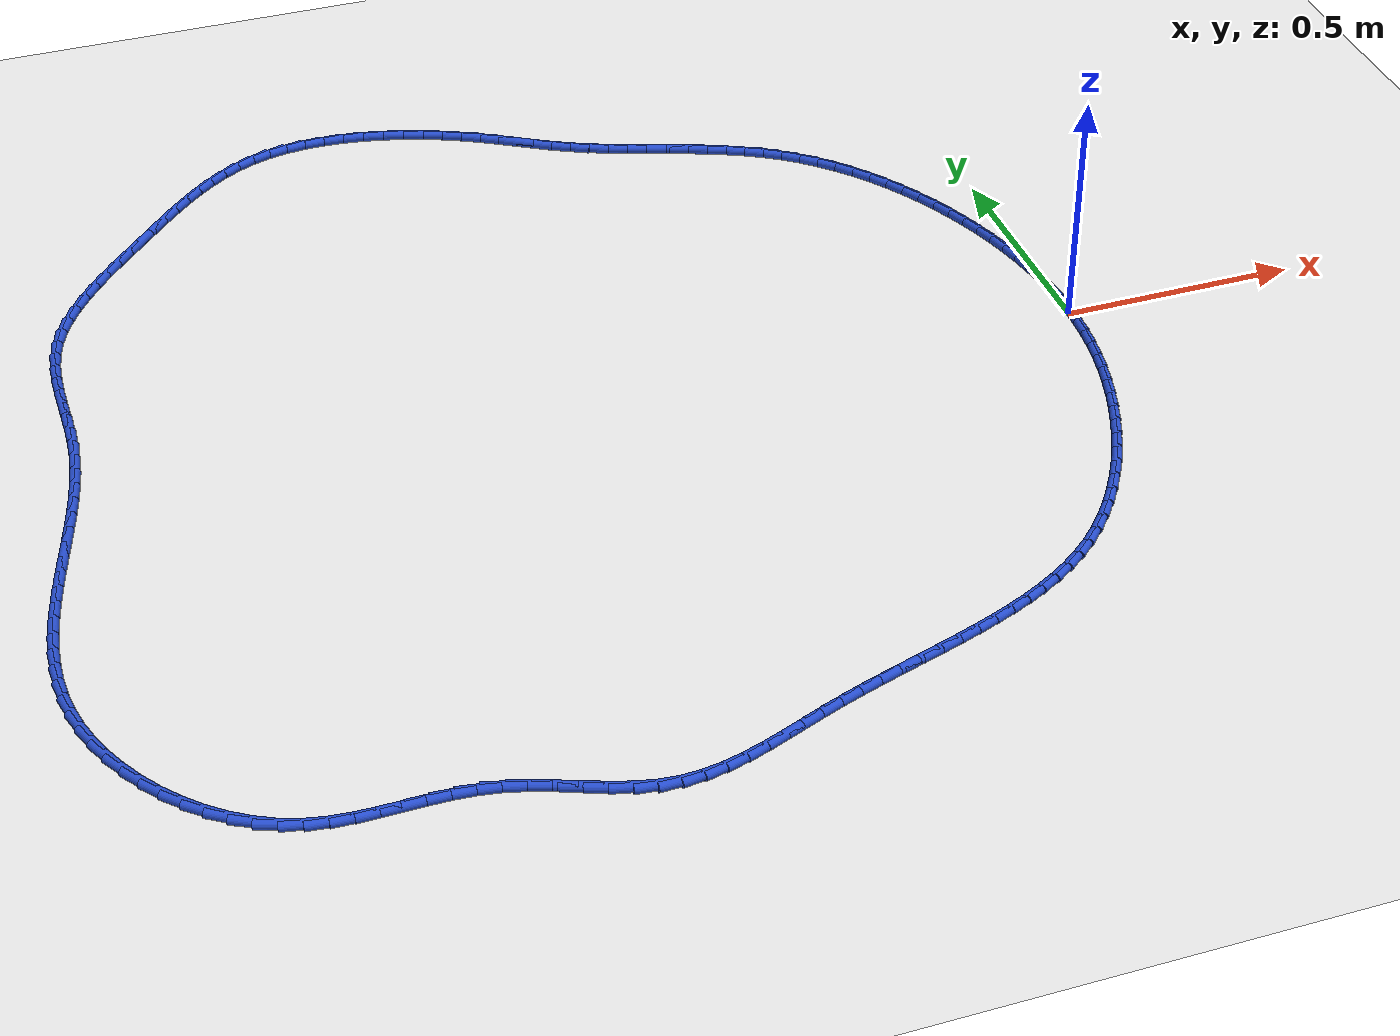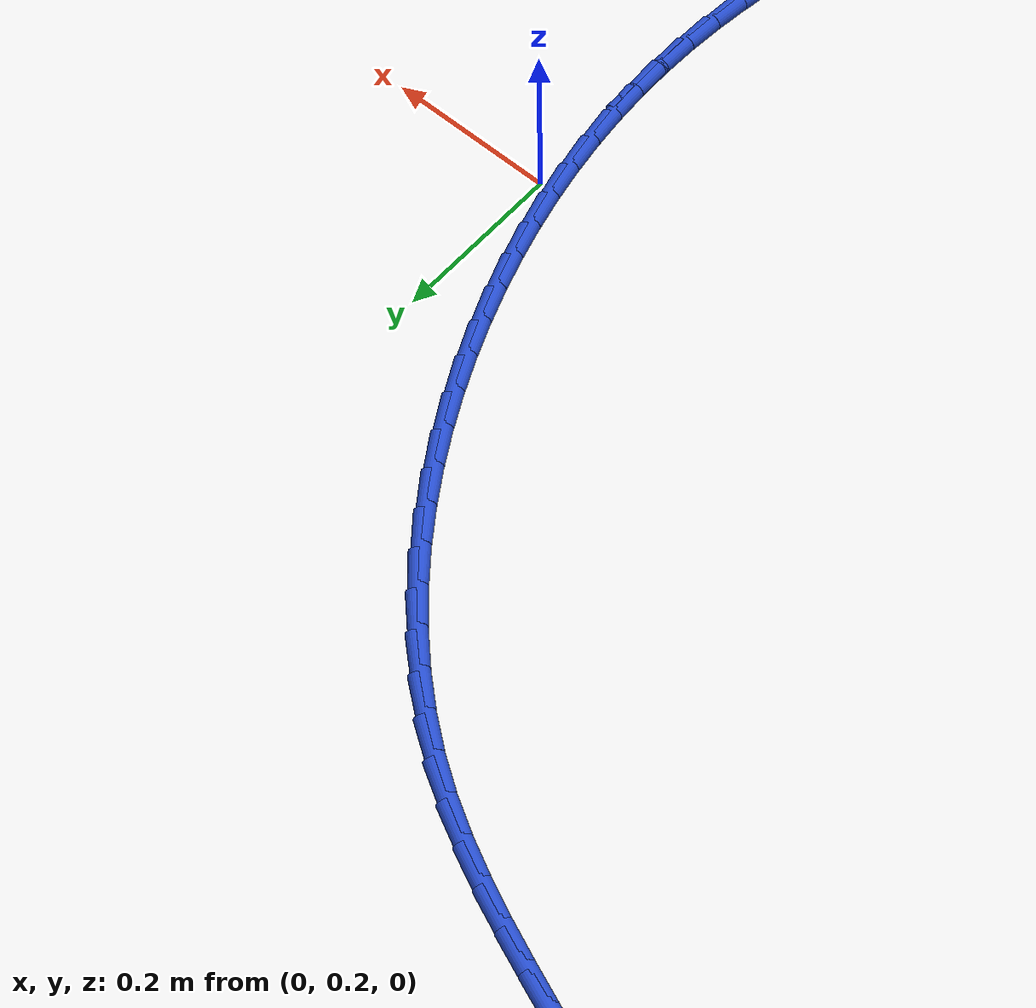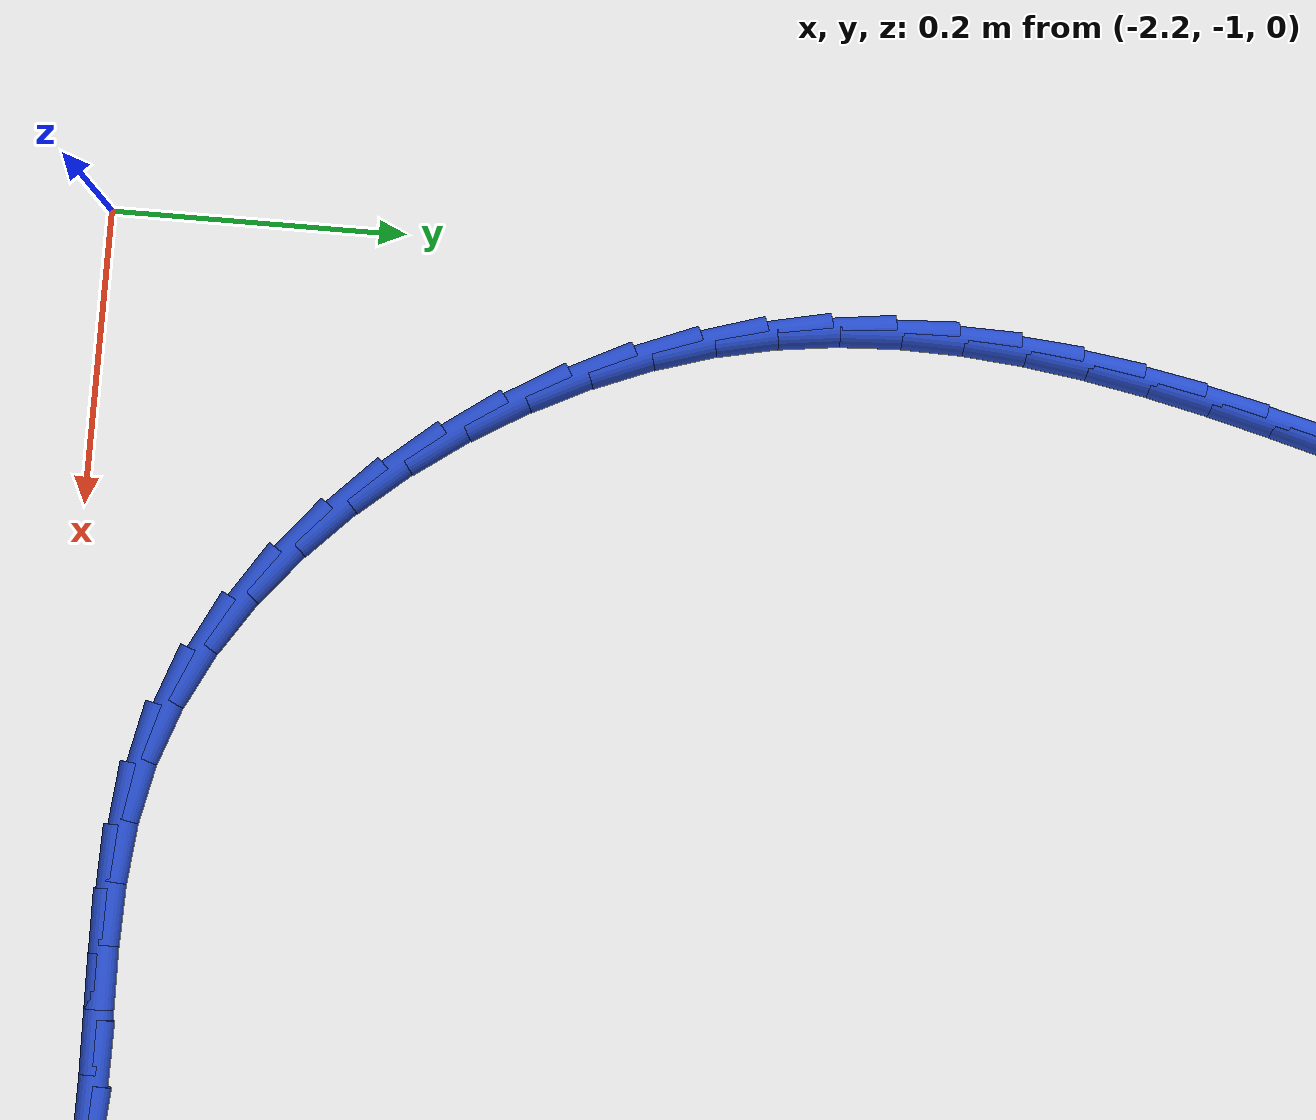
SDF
<sdf version="1.6">
 <world name="default">
  <light name="sun" type="directional">
   <pose>0 0 10 0 -0 0</pose>
   <diffuse>0.8 0.8 0.8 1</diffuse>
   <specular>0.2 0.2 0.2 1</specular>
   <attenuation>
    <range>1000</range>
    <constant>0.9</constant>
    <linear>0.01</linear>
    <quadratic>0.001</quadratic>
   </attenuation>
   <direction>-0.5 0.1 -0.9</direction>
  </light>
  <model name="ground_plane">
   <static>1</static>
   <link name="link">
    <collision name="collision">
     <geometry><plane><normal>0 0 1</normal><size>100 100</size></plane></geometry>
     <surface><friction><ode><mu>100</mu><mu2>50</mu2></ode></friction></surface>
    </collision>
    <visual name="visual">
     <cast_shadows>0</cast_shadows>
     <geometry><plane><normal>0 0 1</normal><size>100 100</size></plane></geometry>
     <material>
      <script><uri>file://media/materials/scripts/gazebo.material</uri><name>Gazebo/WhiteGlow</name></script>
     </material>
    </visual>
   </link>
  </model>
  <gravity>0 0 -9.8</gravity>
  <magnetic_field>6e-06 2.3e-05 -4.2e-05</magnetic_field>
  <atmosphere type="adiabatic"/>
  <physics name="default_physics" default="0" type="ode">
   <max_step_size>0.001</max_step_size>
   <real_time_factor>1</real_time_factor>
   <real_time_update_rate>1000</real_time_update_rate>
  </physics>
  <scene><ambient>0.4 0.4 0.4 1</ambient><background>0.7 0.7 0.7 1</background><shadows>1</shadows></scene>
  <spherical_coordinates>
   <surface_model>EARTH_WGS84</surface_model>
   <latitude_deg>0</latitude_deg>
   <longitude_deg>0</longitude_deg>
   <elevation>0</elevation>
   <heading_deg>0</heading_deg>
  </spherical_coordinates>
  <model name="line">
   <link name="link_0">
    <pose>0.0 -5.551115123125783e-17 0.01 0 1.57 -1.5499981170288915</pose>
    <collision name="collision">
     <geometry><cylinder><radius>0.01</radius><length>0.08</length></cylinder></geometry>
    </collision>
    <visual name="visual">
     <material>
      <script><name>Gazebo/Blue</name><uri>file://media/materials/scripts/gazebo.material</uri></script>
     </material>
     <geometry><cylinder><radius>0.01</radius><length>0.08</length></cylinder></geometry>
    </visual>
   </link>
   <link name="link_1">
    <pose>-0.0008856358317259259 0.04257617071349047 0.01 0 1.57 -1.5057407503299605</pose>
    <collision name="collision">
     <geometry><cylinder><radius>0.01</radius><length>0.08</length></cylinder></geometry>
    </collision>
    <visual name="visual">
     <material>
      <script><name>Gazebo/Blue</name><uri>file://media/materials/scripts/gazebo.material</uri></script>
     </material>
     <geometry><cylinder><radius>0.01</radius><length>0.08</length></cylinder></geometry>
    </visual>
   </link>
   <link name="link_2">
    <pose>-0.003656804995597007 0.08511301081483776 0.01 0 1.57 -1.462009702250215</pose>
    <collision name="collision">
     <geometry><cylinder><radius>0.01</radius><length>0.08</length></cylinder></geometry>
    </collision>
    <visual name="visual">
     <material>
      <script><name>Gazebo/Blue</name><uri>file://media/materials/scripts/gazebo.material</uri></script>
     </material>
     <geometry><cylinder><radius>0.01</radius><length>0.08</length></cylinder></geometry>
    </visual>
   </link>
   <link name="link_3">
    <pose>-0.008293048256093921 0.12756252683826397 0.01 0 1.57 -1.4188169989387012</pose>
    <collision name="collision">
     <geometry><cylinder><radius>0.01</radius><length>0.08</length></cylinder></geometry>
    </collision>
    <visual name="visual">
     <material>
      <script><name>Gazebo/Blue</name><uri>file://media/materials/scripts/gazebo.material</uri></script>
     </material>
     <geometry><cylinder><radius>0.01</radius><length>0.08</length></cylinder></geometry>
    </visual>
   </link>
   <link name="link_4">
    <pose>-0.0147739063776973 0.1698767253179912 0.01 0 1.57 -1.3761675677630327</pose>
    <collision name="collision">
     <geometry><cylinder><radius>0.01</radius><length>0.08</length></cylinder></geometry>
    </collision>
    <visual name="visual">
     <material>
      <script><name>Gazebo/Blue</name><uri>file://media/materials/scripts/gazebo.material</uri></script>
     </material>
     <geometry><cylinder><radius>0.01</radius><length>0.08</length></cylinder></geometry>
    </visual>
   </link>
   <link name="link_5">
    <pose>-0.023078920124887818 0.21200761278824146 0.01 0 1.57 -1.3340599328503213</pose>
    <collision name="collision">
     <geometry><cylinder><radius>0.01</radius><length>0.08</length></cylinder></geometry>
    </collision>
    <visual name="visual">
     <material>
      <script><name>Gazebo/Blue</name><uri>file://media/materials/scripts/gazebo.material</uri></script>
     </material>
     <geometry><cylinder><radius>0.01</radius><length>0.08</length></cylinder></geometry>
    </visual>
   </link>
   <link name="link_6">
    <pose>-0.03318763026214615 0.25390719578323695 0.01 0 1.57 -1.2924869544186555</pose>
    <collision name="collision">
     <geometry><cylinder><radius>0.01</radius><length>0.08</length></cylinder></geometry>
    </collision>
    <visual name="visual">
     <material>
      <script><name>Gazebo/Blue</name><uri>file://media/materials/scripts/gazebo.material</uri></script>
     </material>
     <geometry><cylinder><radius>0.01</radius><length>0.08</length></cylinder></geometry>
    </visual>
   </link>
   <link name="link_7">
    <pose>-0.045079577553952935 0.29552748083719976 0.01 0 1.57 -1.251436585511176</pose>
    <collision name="collision">
     <geometry><cylinder><radius>0.01</radius><length>0.08</length></cylinder></geometry>
    </collision>
    <visual name="visual">
     <material>
      <script><name>Gazebo/Blue</name><uri>file://media/materials/scripts/gazebo.material</uri></script>
     </material>
     <geometry><cylinder><radius>0.01</radius><length>0.08</length></cylinder></geometry>
    </visual>
   </link>
   <link name="link_8">
    <pose>-0.05873430276478879 0.3368204744843517 0.01 0 1.57 -1.2108926244376155</pose>
    <collision name="collision">
     <geometry><cylinder><radius>0.01</radius><length>0.08</length></cylinder></geometry>
    </collision>
    <visual name="visual">
     <material>
      <script><name>Gazebo/Blue</name><uri>file://media/materials/scripts/gazebo.material</uri></script>
     </material>
     <geometry><cylinder><radius>0.01</radius><length>0.08</length></cylinder></geometry>
    </visual>
   </link>
   <link name="link_9">
    <pose>-0.07413134665913446 0.37773818325891534 0.01 0 1.57 -1.1706423900203649</pose>
    <collision name="collision">
     <geometry><cylinder><radius>0.01</radius><length>0.08</length></cylinder></geometry>
    </collision>
    <visual name="visual">
     <material>
      <script><name>Gazebo/Blue</name><uri>file://media/materials/scripts/gazebo.material</uri></script>
     </material>
     <geometry><cylinder><radius>0.01</radius><length>0.08</length></cylinder></geometry>
    </visual>
   </link>
   <link name="link_10">
    <pose>-0.09125207357381432 0.4182151374503532 0.01 0 1.57 -1.1294338119416778</pose>
    <collision name="collision">
     <geometry><cylinder><radius>0.01</radius><length>0.08</length></cylinder></geometry>
    </collision>
    <visual name="visual">
     <material>
      <script><name>Gazebo/Blue</name><uri>file://media/materials/scripts/gazebo.material</uri></script>
     </material>
     <geometry><cylinder><radius>0.01</radius><length>0.08</length></cylinder></geometry>
    </visual>
   </link>
   <link name="link_11">
    <pose>-0.11008838403140446 0.45808489358547655 0.01 0 1.57 -1.0865246834526134</pose>
    <collision name="collision">
     <geometry><cylinder><radius>0.01</radius><length>0.08</length></cylinder></geometry>
    </collision>
    <visual name="visual">
     <material>
      <script><name>Gazebo/Blue</name><uri>file://media/materials/scripts/gazebo.material</uri></script>
     </material>
     <geometry><cylinder><radius>0.01</radius><length>0.08</length></cylinder></geometry>
    </visual>
   </link>
   <link name="link_12">
    <pose>-0.13063595414563267 0.4971448247321265 0.01 0 1.57 -1.0415426561250383</pose>
    <collision name="collision">
     <geometry><cylinder><radius>0.01</radius><length>0.08</length></cylinder></geometry>
    </collision>
    <visual name="visual">
     <material>
      <script><name>Gazebo/Blue</name><uri>file://media/materials/scripts/gazebo.material</uri></script>
     </material>
     <geometry><cylinder><radius>0.01</radius><length>0.08</length></cylinder></geometry>
    </visual>
   </link>
   <link name="link_13">
    <pose>-0.1528904648598726 0.5351922576731293 0.01 0 1.57 -0.9941126918134973</pose>
    <collision name="collision">
     <geometry><cylinder><radius>0.01</radius><length>0.08</length></cylinder></geometry>
    </collision>
    <visual name="visual">
     <material>
      <script><name>Gazebo/Blue</name><uri>file://media/materials/scripts/gazebo.material</uri></script>
     </material>
     <geometry><cylinder><radius>0.01</radius><length>0.08</length></cylinder></geometry>
    </visual>
   </link>
   <link name="link_14">
    <pose>-0.17684759711749812 0.5720245191913107 0.01 0 1.57 -0.9438587285578655</pose>
    <collision name="collision">
     <geometry><cylinder><radius>0.01</radius><length>0.08</length></cylinder></geometry>
    </collision>
    <visual name="visual">
     <material>
      <script><name>Gazebo/Blue</name><uri>file://media/materials/scripts/gazebo.material</uri></script>
     </material>
     <geometry><cylinder><radius>0.01</radius><length>0.08</length></cylinder></geometry>
    </visual>
   </link>
   <link name="link_15">
    <pose>-0.2025030318618829 0.6074389360694968 0.01 0 1.57 -0.8904100417443507</pose>
    <collision name="collision">
     <geometry><cylinder><radius>0.01</radius><length>0.08</length></cylinder></geometry>
    </collision>
    <visual name="visual">
     <material>
      <script><name>Gazebo/Blue</name><uri>file://media/materials/scripts/gazebo.material</uri></script>
     </material>
     <geometry><cylinder><radius>0.01</radius><length>0.08</length></cylinder></geometry>
    </visual>
   </link>
   <link name="link_16">
    <pose>-0.2298524500364007 0.6412328350905137 0.01 0 1.57 -0.8334129517244118</pose>
    <collision name="collision">
     <geometry><cylinder><radius>0.01</radius><length>0.08</length></cylinder></geometry>
    </collision>
    <visual name="visual">
     <material>
      <script><name>Gazebo/Blue</name><uri>file://media/materials/scripts/gazebo.material</uri></script>
     </material>
     <geometry><cylinder><radius>0.01</radius><length>0.08</length></cylinder></geometry>
    </visual>
   </link>
   <link name="link_17">
    <pose>-0.2588915325844253 0.6732035430371872 0.01 0 1.57 -0.7725491331180838</pose>
    <collision name="collision">
     <geometry><cylinder><radius>0.01</radius><length>0.08</length></cylinder></geometry>
    </collision>
    <visual name="visual">
     <material>
      <script><name>Gazebo/Blue</name><uri>file://media/materials/scripts/gazebo.material</uri></script>
     </material>
     <geometry><cylinder><radius>0.01</radius><length>0.08</length></cylinder></geometry>
    </visual>
   </link>
   <link name="link_18">
    <pose>-0.2896159604493304 0.7031483866923433 0.01 0 1.57 -0.707561547577496</pose>
    <collision name="collision">
     <geometry><cylinder><radius>0.01</radius><length>0.08</length></cylinder></geometry>
    </collision>
    <visual name="visual">
     <material>
      <script><name>Gazebo/Blue</name><uri>file://media/materials/scripts/gazebo.material</uri></script>
     </material>
     <geometry><cylinder><radius>0.01</radius><length>0.08</length></cylinder></geometry>
    </visual>
   </link>
   <link name="link_19">
    <pose>-0.32202141457448974 0.7308646928388076 0.01 0 1.57 -0.6382882150715242</pose>
    <collision name="collision">
     <geometry><cylinder><radius>0.01</radius><length>0.08</length></cylinder></geometry>
    </collision>
    <visual name="visual">
     <material>
      <script><name>Gazebo/Blue</name><uri>file://media/materials/scripts/gazebo.material</uri></script>
     </material>
     <geometry><cylinder><radius>0.01</radius><length>0.08</length></cylinder></geometry>
    </visual>
   </link>
   <link name="link_20">
    <pose>-0.3561035759032771 0.7561497882594069 0.01 0 1.57 -0.5650246276006865</pose>
    <collision name="collision">
     <geometry><cylinder><radius>0.01</radius><length>0.08</length></cylinder></geometry>
    </collision>
    <visual name="visual">
     <material>
      <script><name>Gazebo/Blue</name><uri>file://media/materials/scripts/gazebo.material</uri></script>
     </material>
     <geometry><cylinder><radius>0.01</radius><length>0.08</length></cylinder></geometry>
    </visual>
   </link>
   <link name="link_21">
    <pose>-0.3918528012605095 0.7788137729437641 0.01 0 1.57 -0.49573536355720615</pose>
    <collision name="collision">
     <geometry><cylinder><radius>0.01</radius><length>0.08</length></cylinder></geometry>
    </collision>
    <visual name="visual">
     <material>
      <script><name>Gazebo/Blue</name><uri>file://media/materials/scripts/gazebo.material</uri></script>
     </material>
     <geometry><cylinder><radius>0.01</radius><length>0.08</length></cylinder></geometry>
    </visual>
   </link>
   <link name="link_22">
    <pose>-0.42913164901348166 0.7989733508966008 0.01 0 1.57 -0.43876324556015356</pose>
    <collision name="collision">
     <geometry><cylinder><radius>0.01</radius><length>0.08</length></cylinder></geometry>
    </collision>
    <visual name="visual">
     <material>
      <script><name>Gazebo/Blue</name><uri>file://media/materials/scripts/gazebo.material</uri></script>
     </material>
     <geometry><cylinder><radius>0.01</radius><length>0.08</length></cylinder></geometry>
    </visual>
   </link>
   <link name="link_23">
    <pose>-0.4676718378916704 0.8170591262984815 0.01 0 1.57 -0.39451289227731745</pose>
    <collision name="collision">
     <geometry><cylinder><radius>0.01</radius><length>0.08</length></cylinder></geometry>
    </collision>
    <visual name="visual">
     <material>
      <script><name>Gazebo/Blue</name><uri>file://media/materials/scripts/gazebo.material</uri></script>
     </material>
     <geometry><cylinder><radius>0.01</radius><length>0.08</length></cylinder></geometry>
    </visual>
   </link>
   <link name="link_24">
    <pose>-0.5071991541644761 0.833515936021932 0.01 0 1.57 -0.3627429069451114</pose>
    <collision name="collision">
     <geometry><cylinder><radius>0.01</radius><length>0.08</length></cylinder></geometry>
    </collision>
    <visual name="visual">
     <material>
      <script><name>Gazebo/Blue</name><uri>file://media/materials/scripts/gazebo.material</uri></script>
     </material>
     <geometry><cylinder><radius>0.01</radius><length>0.08</length></cylinder></geometry>
    </visual>
   </link>
   <link name="link_25">
    <pose>-0.5474393841012988 0.8487886169394774 0.01 0 1.57 -0.3431373001296187</pose>
    <collision name="collision">
     <geometry><cylinder><radius>0.01</radius><length>0.08</length></cylinder></geometry>
    </collision>
    <visual name="visual">
     <material>
      <script><name>Gazebo/Blue</name><uri>file://media/materials/scripts/gazebo.material</uri></script>
     </material>
     <geometry><cylinder><radius>0.01</radius><length>0.08</length></cylinder></geometry>
    </visual>
   </link>
   <link name="link_26">
    <pose>-0.588118313971539 0.8633220059236434 0.01 0 1.57 -0.33544712345928573</pose>
    <collision name="collision">
     <geometry><cylinder><radius>0.01</radius><length>0.08</length></cylinder></geometry>
    </collision>
    <visual name="visual">
     <material>
      <script><name>Gazebo/Blue</name><uri>file://media/materials/scripts/gazebo.material</uri></script>
     </material>
     <geometry><cylinder><radius>0.01</radius><length>0.08</length></cylinder></geometry>
    </visual>
   </link>
   <link name="link_27">
    <pose>-0.6289617300445971 0.8775609398469554 0.01 0 1.57 -0.3395702644666284</pose>
    <collision name="collision">
     <geometry><cylinder><radius>0.01</radius><length>0.08</length></cylinder></geometry>
    </collision>
    <visual name="visual">
     <material>
      <script><name>Gazebo/Blue</name><uri>file://media/materials/scripts/gazebo.material</uri></script>
     </material>
     <geometry><cylinder><radius>0.01</radius><length>0.08</length></cylinder></geometry>
    </visual>
   </link>
   <link name="link_28">
    <pose>-0.669695418589873 0.8919502555819385 0.01 0 1.57 -0.3555811189852587</pose>
    <collision name="collision">
     <geometry><cylinder><radius>0.01</radius><length>0.08</length></cylinder></geometry>
    </collision>
    <visual name="visual">
     <material>
      <script><name>Gazebo/Blue</name><uri>file://media/materials/scripts/gazebo.material</uri></script>
     </material>
     <geometry><cylinder><radius>0.01</radius><length>0.08</length></cylinder></geometry>
    </visual>
   </link>
   <link name="link_29">
    <pose>-0.7100451658767669 0.9069347900011184 0.01 0 1.57 -0.38371566051816947</pose>
    <collision name="collision">
     <geometry><cylinder><radius>0.01</radius><length>0.08</length></cylinder></geometry>
    </collision>
    <visual name="visual">
     <material>
      <script><name>Gazebo/Blue</name><uri>file://media/materials/scripts/gazebo.material</uri></script>
     </material>
     <geometry><cylinder><radius>0.01</radius><length>0.08</length></cylinder></geometry>
    </visual>
   </link>
   <link name="link_30">
    <pose>-0.7497367581746791 0.9229593799770206 0.01 0 1.57 -0.42430834170495013</pose>
    <collision name="collision">
     <geometry><cylinder><radius>0.01</radius><length>0.08</length></cylinder></geometry>
    </collision>
    <visual name="visual">
     <material>
      <script><name>Gazebo/Blue</name><uri>file://media/materials/scripts/gazebo.material</uri></script>
     </material>
     <geometry><cylinder><radius>0.01</radius><length>0.08</length></cylinder></geometry>
    </visual>
   </link>
   <link name="link_31">
    <pose>-0.7884959817530102 0.9404688623821702 0.01 0 1.57 -0.4748534811117812</pose>
    <collision name="collision">
     <geometry><cylinder><radius>0.01</radius><length>0.08</length></cylinder></geometry>
    </collision>
    <visual name="visual">
     <material>
      <script><name>Gazebo/Blue</name><uri>file://media/materials/scripts/gazebo.material</uri></script>
     </material>
     <geometry><cylinder><radius>0.01</radius><length>0.08</length></cylinder></geometry>
    </visual>
   </link>
   <link name="link_32">
    <pose>-0.8261205521553765 0.9598111595466888 0.01 0 1.57 -0.5148686549594313</pose>
    <collision name="collision">
     <geometry><cylinder><radius>0.01</radius><length>0.08</length></cylinder></geometry>
    </collision>
    <visual name="visual">
     <material>
      <script><name>Gazebo/Blue</name><uri>file://media/materials/scripts/gazebo.material</uri></script>
     </material>
     <geometry><cylinder><radius>0.01</radius><length>0.08</length></cylinder></geometry>
    </visual>
   </link>
   <link name="link_33">
    <pose>-0.8629270453423252 0.9806351026389025 0.01 0 1.57 -0.5349287387337488</pose>
    <collision name="collision">
     <geometry><cylinder><radius>0.01</radius><length>0.08</length></cylinder></geometry>
    </collision>
    <visual name="visual">
     <material>
      <script><name>Gazebo/Blue</name><uri>file://media/materials/scripts/gazebo.material</uri></script>
     </material>
     <geometry><cylinder><radius>0.01</radius><length>0.08</length></cylinder></geometry>
    </visual>
   </link>
   <link name="link_34">
    <pose>-0.8994596980359985 1.0022827820908562 0.01 0 1.57 -0.5350034224480695</pose>
    <collision name="collision">
     <geometry><cylinder><radius>0.01</radius><length>0.08</length></cylinder></geometry>
    </collision>
    <visual name="visual">
     <material>
      <script><name>Gazebo/Blue</name><uri>file://media/materials/scripts/gazebo.material</uri></script>
     </material>
     <geometry><cylinder><radius>0.01</radius><length>0.08</length></cylinder></geometry>
    </visual>
   </link>
   <link name="link_35">
    <pose>-0.9362637200239923 1.0240949772662662 0.01 0 1.57 -0.5155318981041329</pose>
    <collision name="collision">
     <geometry><cylinder><radius>0.01</radius><length>0.08</length></cylinder></geometry>
    </collision>
    <visual name="visual">
     <material>
      <script><name>Gazebo/Blue</name><uri>file://media/materials/scripts/gazebo.material</uri></script>
     </material>
     <geometry><cylinder><radius>0.01</radius><length>0.08</length></cylinder></geometry>
    </visual>
   </link>
   <link name="link_36">
    <pose>-0.9738843210939037 1.0454124675288496 0.01 0 1.57 -0.47739131307596844</pose>
    <collision name="collision">
     <geometry><cylinder><radius>0.01</radius><length>0.08</length></cylinder></geometry>
    </collision>
    <visual name="visual">
     <material>
      <script><name>Gazebo/Blue</name><uri>file://media/materials/scripts/gazebo.material</uri></script>
     </material>
     <geometry><cylinder><radius>0.01</radius><length>0.08</length></cylinder></geometry>
    </visual>
   </link>
   <link name="link_37">
    <pose>-1.0128646427172918 1.06557697229822 0.01 0 1.57 -0.4269977257239599</pose>
    <collision name="collision">
     <geometry><cylinder><radius>0.01</radius><length>0.08</length></cylinder></geometry>
    </collision>
    <visual name="visual">
     <material>
      <script><name>Gazebo/Blue</name><uri>file://media/materials/scripts/gazebo.material</uri></script>
     </material>
     <geometry><cylinder><radius>0.01</radius><length>0.08</length></cylinder></geometry>
    </visual>
   </link>
   <link name="link_38">
    <pose>-1.0534748251771269 1.0840542908603117 0.01 0 1.57 -0.3746542257135561</pose>
    <collision name="collision">
     <geometry><cylinder><radius>0.01</radius><length>0.08</length></cylinder></geometry>
    </collision>
    <visual name="visual">
     <material>
      <script><name>Gazebo/Blue</name><uri>file://media/materials/scripts/gazebo.material</uri></script>
     </material>
     <geometry><cylinder><radius>0.01</radius><length>0.08</length></cylinder></geometry>
    </visual>
   </link>
   <link name="link_39">
    <pose>-1.0954421093681261 1.1005569719158432 0.01 0 1.57 -0.32050676634650327</pose>
    <collision name="collision">
     <geometry><cylinder><radius>0.01</radius><length>0.08</length></cylinder></geometry>
    </collision>
    <visual name="visual">
     <material>
      <script><name>Gazebo/Blue</name><uri>file://media/materials/scripts/gazebo.material</uri></script>
     </material>
     <geometry><cylinder><radius>0.01</radius><length>0.08</length></cylinder></geometry>
    </visual>
   </link>
   <link name="link_40">
    <pose>-1.1384295521239123 1.1148267360155222 0.01 0 1.57 -0.2634448168717703</pose>
    <collision name="collision">
     <geometry><cylinder><radius>0.01</radius><length>0.08</length></cylinder></geometry>
    </collision>
    <visual name="visual">
     <material>
      <script><name>Gazebo/Blue</name><uri>file://media/materials/scripts/gazebo.material</uri></script>
     </material>
     <geometry><cylinder><radius>0.01</radius><length>0.08</length></cylinder></geometry>
    </visual>
   </link>
   <link name="link_41">
    <pose>-1.1821002102781097 1.1266053037100558 0.01 0 1.57 -0.20232114689277186</pose>
    <collision name="collision">
     <geometry><cylinder><radius>0.01</radius><length>0.08</length></cylinder></geometry>
    </collision>
    <visual name="visual">
     <material>
      <script><name>Gazebo/Blue</name><uri>file://media/materials/scripts/gazebo.material</uri></script>
     </material>
     <geometry><cylinder><radius>0.01</radius><length>0.08</length></cylinder></geometry>
    </visual>
   </link>
   <link name="link_42">
    <pose>-1.2261171406643419 1.135634395550152 0.01 0 1.57 -0.1359236281425983</pose>
    <collision name="collision">
     <geometry><cylinder><radius>0.01</radius><length>0.08</length></cylinder></geometry>
    </collision>
    <visual name="visual">
     <material>
      <script><name>Gazebo/Blue</name><uri>file://media/materials/scripts/gazebo.material</uri></script>
     </material>
     <geometry><cylinder><radius>0.01</radius><length>0.08</length></cylinder></geometry>
    </visual>
   </link>
   <link name="link_43">
    <pose>-1.2701434001162317 1.1416557320865175 0.01 0 1.57 -0.06296898045122024</pose>
    <collision name="collision">
     <geometry><cylinder><radius>0.01</radius><length>0.08</length></cylinder></geometry>
    </collision>
    <visual name="visual">
     <material>
      <script><name>Gazebo/Blue</name><uri>file://media/materials/scripts/gazebo.material</uri></script>
     </material>
     <geometry><cylinder><radius>0.01</radius><length>0.08</length></cylinder></geometry>
    </visual>
   </link>
   <link name="link_44">
    <pose>-1.313842045467404 1.1444110338698605 0.01 0 1.57 0.017867941724929177</pose>
    <collision name="collision">
     <geometry><cylinder><radius>0.01</radius><length>0.08</length></cylinder></geometry>
    </collision>
    <visual name="visual">
     <material>
      <script><name>Gazebo/Blue</name><uri>file://media/materials/scripts/gazebo.material</uri></script>
     </material>
     <geometry><cylinder><radius>0.01</radius><length>0.08</length></cylinder></geometry>
    </visual>
   </link>
   <link name="link_45">
    <pose>-1.3568761335514812 1.1436420214508887 0.01 0 1.57 0.10786723949178444</pose>
    <collision name="collision">
     <geometry><cylinder><radius>0.01</radius><length>0.08</length></cylinder></geometry>
    </collision>
    <visual name="visual">
     <material>
      <script><name>Gazebo/Blue</name><uri>file://media/materials/scripts/gazebo.material</uri></script>
     </material>
     <geometry><cylinder><radius>0.01</radius><length>0.08</length></cylinder></geometry>
    </visual>
   </link>
   <link name="link_46">
    <pose>-1.3989087212020876 1.1390904153803083 0.01 0 1.57 0.20809126432651076</pose>
    <collision name="collision">
     <geometry><cylinder><radius>0.01</radius><length>0.08</length></cylinder></geometry>
    </collision>
    <visual name="visual">
     <material>
      <script><name>Gazebo/Blue</name><uri>file://media/materials/scripts/gazebo.material</uri></script>
     </material>
     <geometry><cylinder><radius>0.01</radius><length>0.08</length></cylinder></geometry>
    </visual>
   </link>
   <link name="link_47">
    <pose>-1.4396028652528463 1.130497936208828 0.01 0 1.57 0.31896822076236286</pose>
    <collision name="collision">
     <geometry><cylinder><radius>0.01</radius><length>0.08</length></cylinder></geometry>
    </collision>
    <visual name="visual">
     <material>
      <script><name>Gazebo/Blue</name><uri>file://media/materials/scripts/gazebo.material</uri></script>
     </material>
     <geometry><cylinder><radius>0.01</radius><length>0.08</length></cylinder></geometry>
    </visual>
   </link>
   <link name="link_48">
    <pose>-1.4786251119743778 1.117611045731805 0.01 0 1.57 0.4317569409458788</pose>
    <collision name="collision">
     <geometry><cylinder><radius>0.01</radius><length>0.08</length></cylinder></geometry>
    </collision>
    <visual name="visual">
     <material>
      <script><name>Gazebo/Blue</name><uri>file://media/materials/scripts/gazebo.material</uri></script>
     </material>
     <geometry><cylinder><radius>0.01</radius><length>0.08</length></cylinder></geometry>
    </visual>
   </link>
   <link name="link_49">
    <pose>-1.5158504911998227 1.100459481120133 0.01 0 1.57 0.5315474989459231</pose>
    <collision name="collision">
     <geometry><cylinder><radius>0.01</radius><length>0.08</length></cylinder></geometry>
    </collision>
    <visual name="visual">
     <material>
      <script><name>Gazebo/Blue</name><uri>file://media/materials/scripts/gazebo.material</uri></script>
     </material>
     <geometry><cylinder><radius>0.01</radius><length>0.08</length></cylinder></geometry>
    </visual>
   </link>
   <link name="link_50">
    <pose>-1.5514766757755392 1.0795113681621415 0.01 0 1.57 0.615846117902603</pose>
    <collision name="collision">
     <geometry><cylinder><radius>0.01</radius><length>0.08</length></cylinder></geometry>
    </collision>
    <visual name="visual">
     <material>
      <script><name>Gazebo/Blue</name><uri>file://media/materials/scripts/gazebo.material</uri></script>
     </material>
     <geometry><cylinder><radius>0.01</radius><length>0.08</length></cylinder></geometry>
    </visual>
   </link>
   <link name="link_51">
    <pose>-1.5857290336706389 1.0552724631730186 0.01 0 1.57 0.6846235005672875</pose>
    <collision name="collision">
     <geometry><cylinder><radius>0.01</radius><length>0.08</length></cylinder></geometry>
    </collision>
    <visual name="visual">
     <material>
      <script><name>Gazebo/Blue</name><uri>file://media/materials/scripts/gazebo.material</uri></script>
     </material>
     <geometry><cylinder><radius>0.01</radius><length>0.08</length></cylinder></geometry>
    </visual>
   </link>
   <link name="link_52">
    <pose>-1.6188329328542335 1.028248522467953 0.01 0 1.57 0.7386300824438513</pose>
    <collision name="collision">
     <geometry><cylinder><radius>0.01</radius><length>0.08</length></cylinder></geometry>
    </collision>
    <visual name="visual">
     <material>
      <script><name>Gazebo/Blue</name><uri>file://media/materials/scripts/gazebo.material</uri></script>
     </material>
     <geometry><cylinder><radius>0.01</radius><length>0.08</length></cylinder></geometry>
    </visual>
   </link>
   <link name="link_53">
    <pose>-1.6510137412954358 0.9989453023621324 0.01 0 1.57 0.7789029927780443</pose>
    <collision name="collision">
     <geometry><cylinder><radius>0.01</radius><length>0.08</length></cylinder></geometry>
    </collision>
    <visual name="visual">
     <material>
      <script><name>Gazebo/Blue</name><uri>file://media/materials/scripts/gazebo.material</uri></script>
     </material>
     <geometry><cylinder><radius>0.01</radius><length>0.08</length></cylinder></geometry>
    </visual>
   </link>
   <link name="link_54">
    <pose>-1.682496826963357 0.9678685591707453 0.01 0 1.57 0.806447441847633</pose>
    <collision name="collision">
     <geometry><cylinder><radius>0.01</radius><length>0.08</length></cylinder></geometry>
    </collision>
    <visual name="visual">
     <material>
      <script><name>Gazebo/Blue</name><uri>file://media/materials/scripts/gazebo.material</uri></script>
     </material>
     <geometry><cylinder><radius>0.01</radius><length>0.08</length></cylinder></geometry>
    </visual>
   </link>
   <link name="link_55">
    <pose>-1.7135075578271097 0.9355240492089798 0.01 0 1.57 0.82206196255046</pose>
    <collision name="collision">
     <geometry><cylinder><radius>0.01</radius><length>0.08</length></cylinder></geometry>
    </collision>
    <visual name="visual">
     <material>
      <script><name>Gazebo/Blue</name><uri>file://media/materials/scripts/gazebo.material</uri></script>
     </material>
     <geometry><cylinder><radius>0.01</radius><length>0.08</length></cylinder></geometry>
    </visual>
   </link>
   <link name="link_56">
    <pose>-1.7442713018558058 0.9024175287920229 0.01 0 1.57 0.8262953286771116</pose>
    <collision name="collision">
     <geometry><cylinder><radius>0.01</radius><length>0.08</length></cylinder></geometry>
    </collision>
    <visual name="visual">
     <material>
      <script><name>Gazebo/Blue</name><uri>file://media/materials/scripts/gazebo.material</uri></script>
     </material>
     <geometry><cylinder><radius>0.01</radius><length>0.08</length></cylinder></geometry>
    </visual>
   </link>
   <link name="link_57">
    <pose>-1.775012148666819 0.869053512135963 0.01 0 1.57 0.8255865061730806</pose>
    <collision name="collision">
     <geometry><cylinder><radius>0.01</radius><length>0.08</length></cylinder></geometry>
    </collision>
    <visual name="visual">
     <material>
      <script><name>Gazebo/Blue</name><uri>file://media/materials/scripts/gazebo.material</uri></script>
     </material>
     <geometry><cylinder><radius>0.01</radius><length>0.08</length></cylinder></geometry>
    </visual>
   </link>
   <link name="link_58">
    <pose>-1.8057509955805144 0.8357390834681213 0.01 0 1.57 0.8330159238079928</pose>
    <collision name="collision">
     <geometry><cylinder><radius>0.01</radius><length>0.08</length></cylinder></geometry>
    </collision>
    <visual name="visual">
     <material>
      <script><name>Gazebo/Blue</name><uri>file://media/materials/scripts/gazebo.material</uri></script>
     </material>
     <geometry><cylinder><radius>0.01</radius><length>0.08</length></cylinder></geometry>
    </visual>
   </link>
   <link name="link_59">
    <pose>-1.8360848799427312 0.8023694872401915 0.01 0 1.57 0.8504589798484335</pose>
    <collision name="collision">
     <geometry><cylinder><radius>0.01</radius><length>0.08</length></cylinder></geometry>
    </collision>
    <visual name="visual">
     <material>
      <script><name>Gazebo/Blue</name><uri>file://media/materials/scripts/gazebo.material</uri></script>
     </material>
     <geometry><cylinder><radius>0.01</radius><length>0.08</length></cylinder></geometry>
    </visual>
   </link>
   <link name="link_60">
    <pose>-1.8655577965014776 0.7687884295352961 0.01 0 1.57 0.8784048352163771</pose>
    <collision name="collision">
     <geometry><cylinder><radius>0.01</radius><length>0.08</length></cylinder></geometry>
    </collision>
    <visual name="visual">
     <material>
      <script><name>Gazebo/Blue</name><uri>file://media/materials/scripts/gazebo.material</uri></script>
     </material>
     <geometry><cylinder><radius>0.01</radius><length>0.08</length></cylinder></geometry>
    </visual>
   </link>
   <link name="link_61">
    <pose>-1.8937137400047601 0.7348396164365565 0.01 0 1.57 0.9175587481591925</pose>
    <collision name="collision">
     <geometry><cylinder><radius>0.01</radius><length>0.08</length></cylinder></geometry>
    </collision>
    <visual name="visual">
     <material>
      <script><name>Gazebo/Blue</name><uri>file://media/materials/scripts/gazebo.material</uri></script>
     </material>
     <geometry><cylinder><radius>0.01</radius><length>0.08</length></cylinder></geometry>
    </visual>
   </link>
   <link name="link_62">
    <pose>-1.9200967052005875 0.7003667540270958 0.01 0 1.57 0.9687765132740612</pose>
    <collision name="collision">
     <geometry><cylinder><radius>0.01</radius><length>0.08</length></cylinder></geometry>
    </collision>
    <visual name="visual">
     <material>
      <script><name>Gazebo/Blue</name><uri>file://media/materials/scripts/gazebo.material</uri></script>
     </material>
     <geometry><cylinder><radius>0.01</radius><length>0.08</length></cylinder></geometry>
    </visual>
   </link>
   <link name="link_63">
    <pose>-1.944250686836966 0.6652135483900354 0.01 0 1.57 1.032932779184081</pose>
    <collision name="collision">
     <geometry><cylinder><radius>0.01</radius><length>0.08</length></cylinder></geometry>
    </collision>
    <visual name="visual">
     <material>
      <script><name>Gazebo/Blue</name><uri>file://media/materials/scripts/gazebo.material</uri></script>
     </material>
     <geometry><cylinder><radius>0.01</radius><length>0.08</length></cylinder></geometry>
    </visual>
   </link>
   <link name="link_64">
    <pose>-1.9657196796619039 0.6292237056084983 0.01 0 1.57 1.1106893223865641</pose>
    <collision name="collision">
     <geometry><cylinder><radius>0.01</radius><length>0.08</length></cylinder></geometry>
    </collision>
    <visual name="visual">
     <material>
      <script><name>Gazebo/Blue</name><uri>file://media/materials/scripts/gazebo.material</uri></script>
     </material>
     <geometry><cylinder><radius>0.01</radius><length>0.08</length></cylinder></geometry>
    </visual>
   </link>
   <link name="link_65">
    <pose>-1.9840476784234078 0.592240931765606 0.01 0 1.57 1.2021419151035606</pose>
    <collision name="collision">
     <geometry><cylinder><radius>0.01</radius><length>0.08</length></cylinder></geometry>
    </collision>
    <visual name="visual">
     <material>
      <script><name>Gazebo/Blue</name><uri>file://media/materials/scripts/gazebo.material</uri></script>
     </material>
     <geometry><cylinder><radius>0.01</radius><length>0.08</length></cylinder></geometry>
    </visual>
   </link>
   <link name="link_66">
    <pose>-1.9987786778694856 0.5541089329444808 0.01 0 1.57 1.30553539822531</pose>
    <collision name="collision">
     <geometry><cylinder><radius>0.01</radius><length>0.08</length></cylinder></geometry>
    </collision>
    <visual name="visual">
     <material>
      <script><name>Gazebo/Blue</name><uri>file://media/materials/scripts/gazebo.material</uri></script>
     </material>
     <geometry><cylinder><radius>0.01</radius><length>0.08</length></cylinder></geometry>
    </visual>
   </link>
   <link name="link_67">
    <pose>-2.009489838312924 0.5146807756699984 0.01 0 1.57 1.4024591504643038</pose>
    <collision name="collision">
     <geometry><cylinder><radius>0.01</radius><length>0.08</length></cylinder></geometry>
    </collision>
    <visual name="visual">
     <material>
      <script><name>Gazebo/Blue</name><uri>file://media/materials/scripts/gazebo.material</uri></script>
     </material>
     <geometry><cylinder><radius>0.01</radius><length>0.08</length></cylinder></geometry>
    </visual>
   </link>
   <link name="link_68">
    <pose>-2.0164047186364913 0.47399196196010696 0.01 0 1.57 1.4769411322177208</pose>
    <collision name="collision">
     <geometry><cylinder><radius>0.01</radius><length>0.08</length></cylinder></geometry>
    </collision>
    <visual name="visual">
     <material>
      <script><name>Gazebo/Blue</name><uri>file://media/materials/scripts/gazebo.material</uri></script>
     </material>
     <geometry><cylinder><radius>0.01</radius><length>0.08</length></cylinder></geometry>
    </visual>
   </link>
   <link name="link_69">
    <pose>-2.020334541373556 0.4322438523492146 0.01 0 1.57 1.5290981531068213</pose>
    <collision name="collision">
     <geometry><cylinder><radius>0.01</radius><length>0.08</length></cylinder></geometry>
    </collision>
    <visual name="visual">
     <material>
      <script><name>Gazebo/Blue</name><uri>file://media/materials/scripts/gazebo.material</uri></script>
     </material>
     <geometry><cylinder><radius>0.01</radius><length>0.08</length></cylinder></geometry>
    </visual>
   </link>
   <link name="link_70">
    <pose>-2.0221119142109956 0.3896438429838205 0.01 0 1.57 1.5602166365020065</pose>
    <collision name="collision">
     <geometry><cylinder><radius>0.01</radius><length>0.08</length></cylinder></geometry>
    </collision>
    <visual name="visual">
     <material>
      <script><name>Gazebo/Blue</name><uri>file://media/materials/scripts/gazebo.material</uri></script>
     </material>
     <geometry><cylinder><radius>0.01</radius><length>0.08</length></cylinder></geometry>
    </visual>
   </link>
   <link name="link_71">
    <pose>-2.0225694448356926 0.34639933001042483 0.01 0 1.57 -1.5701163177592612</pose>
    <collision name="collision">
     <geometry><cylinder><radius>0.01</radius><length>0.08</length></cylinder></geometry>
    </collision>
    <visual name="visual">
     <material>
      <script><name>Gazebo/Blue</name><uri>file://media/materials/scripts/gazebo.material</uri></script>
     </material>
     <geometry><cylinder><radius>0.01</radius><length>0.08</length></cylinder></geometry>
    </visual>
   </link>
   <link name="link_72">
    <pose>-2.022539740934527 0.30271770957552824 0.01 0 1.57 1.5636076625105153</pose>
    <collision name="collision">
     <geometry><cylinder><radius>0.01</radius><length>0.08</length></cylinder></geometry>
    </collision>
    <visual name="visual">
     <material>
      <script><name>Gazebo/Blue</name><uri>file://media/materials/scripts/gazebo.material</uri></script>
     </material>
     <geometry><cylinder><radius>0.01</radius><length>0.08</length></cylinder></geometry>
    </visual>
   </link>
   <link name="link_73">
    <pose>-2.0228554101943783 0.2588063778256298 0.01 0 1.57 1.5368115536102331</pose>
    <collision name="collision">
     <geometry><cylinder><radius>0.01</radius><length>0.08</length></cylinder></geometry>
    </collision>
    <visual name="visual">
     <material>
      <script><name>Gazebo/Blue</name><uri>file://media/materials/scripts/gazebo.material</uri></script>
     </material>
     <geometry><cylinder><radius>0.01</radius><length>0.08</length></cylinder></geometry>
    </visual>
   </link>
   <link name="link_74">
    <pose>-2.024349060302127 0.21487273090723066 0.01 0 1.57 1.4912900151780408</pose>
    <collision name="collision">
     <geometry><cylinder><radius>0.01</radius><length>0.08</length></cylinder></geometry>
    </collision>
    <visual name="visual">
     <material>
      <script><name>Gazebo/Blue</name><uri>file://media/materials/scripts/gazebo.material</uri></script>
     </material>
     <geometry><cylinder><radius>0.01</radius><length>0.08</length></cylinder></geometry>
    </visual>
   </link>
   <link name="link_75">
    <pose>-2.0278349789806054 0.17112060123102787 0.01 0 1.57 1.439061428745569</pose>
    <collision name="collision">
     <geometry><cylinder><radius>0.01</radius><length>0.08</length></cylinder></geometry>
    </collision>
    <visual name="visual">
     <material>
      <script><name>Gazebo/Blue</name><uri>file://media/materials/scripts/gazebo.material</uri></script>
     </material>
     <geometry><cylinder><radius>0.01</radius><length>0.08</length></cylinder></geometry>
    </visual>
   </link>
   <link name="link_76">
    <pose>-2.033594902526976 0.12765022533945006 0.01 0 1.57 1.3941419790321197</pose>
    <collision name="collision">
     <geometry><cylinder><radius>0.01</radius><length>0.08</length></cylinder></geometry>
    </collision>
    <visual name="visual">
     <material>
      <script><name>Gazebo/Blue</name><uri>file://media/materials/scripts/gazebo.material</uri></script>
     </material>
     <geometry><cylinder><radius>0.01</radius><length>0.08</length></cylinder></geometry>
    </visual>
   </link>
   <link name="link_77">
    <pose>-2.041307766468012 0.08444457848110261 0.01 0 1.57 1.3573525213867943</pose>
    <collision name="collision">
     <geometry><cylinder><radius>0.01</radius><length>0.08</length></cylinder></geometry>
    </collision>
    <visual name="visual">
     <material>
      <script><name>Gazebo/Blue</name><uri>file://media/materials/scripts/gazebo.material</uri></script>
     </material>
     <geometry><cylinder><radius>0.01</radius><length>0.08</length></cylinder></geometry>
    </visual>
   </link>
   <link name="link_78">
    <pose>-2.050620068843038 0.04148032592302804 0.01 0 1.57 1.3286447415477207</pose>
    <collision name="collision">
     <geometry><cylinder><radius>0.01</radius><length>0.08</length></cylinder></geometry>
    </collision>
    <visual name="visual">
     <material>
      <script><name>Gazebo/Blue</name><uri>file://media/materials/scripts/gazebo.material</uri></script>
     </material>
     <geometry><cylinder><radius>0.01</radius><length>0.08</length></cylinder></geometry>
    </visual>
   </link>
   <link name="link_79">
    <pose>-2.061178307691376 -0.0012658670677298976 0.01 0 1.57 1.3079219242878306</pose>
    <collision name="collision">
     <geometry><cylinder><radius>0.01</radius><length>0.08</length></cylinder></geometry>
    </collision>
    <visual name="visual">
     <material>
      <script><name>Gazebo/Blue</name><uri>file://media/materials/scripts/gazebo.material</uri></script>
     </material>
     <geometry><cylinder><radius>0.01</radius><length>0.08</length></cylinder></geometry>
    </visual>
   </link>
   <link name="link_80">
    <pose>-2.0726289810523526 -0.0438173352241285 0.01 0 1.57 1.2950943270776047</pose>
    <collision name="collision">
     <geometry><cylinder><radius>0.01</radius><length>0.08</length></cylinder></geometry>
    </collision>
    <visual name="visual">
     <material>
      <script><name>Gazebo/Blue</name><uri>file://media/materials/scripts/gazebo.material</uri></script>
     </material>
     <geometry><cylinder><radius>0.01</radius><length>0.08</length></cylinder></geometry>
    </visual>
   </link>
   <link name="link_81">
    <pose>-2.084618586965292 -0.08619741327912472 0.01 0 1.57 1.2901176989705136</pose>
    <collision name="collision">
     <geometry><cylinder><radius>0.01</radius><length>0.08</length></cylinder></geometry>
    </collision>
    <visual name="visual">
     <material>
      <script><name>Gazebo/Blue</name><uri>file://media/materials/scripts/gazebo.material</uri></script>
     </material>
     <geometry><cylinder><radius>0.01</radius><length>0.08</length></cylinder></geometry>
    </visual>
   </link>
   <link name="link_82">
    <pose>-2.0967936234695177 -0.12842943596567627 0.01 0 1.57 1.2930169511335645</pose>
    <collision name="collision">
     <geometry><cylinder><radius>0.01</radius><length>0.08</length></cylinder></geometry>
    </collision>
    <visual name="visual">
     <material>
      <script><name>Gazebo/Blue</name><uri>file://media/materials/scripts/gazebo.material</uri></script>
     </material>
     <geometry><cylinder><radius>0.01</radius><length>0.08</length></cylinder></geometry>
    </visual>
   </link>
   <link name="link_83">
    <pose>-2.108800588604355 -0.1705367380167386 0.01 0 1.57 1.3038966490480937</pose>
    <collision name="collision">
     <geometry><cylinder><radius>0.01</radius><length>0.08</length></cylinder></geometry>
    </collision>
    <visual name="visual">
     <material>
      <script><name>Gazebo/Blue</name><uri>file://media/materials/scripts/gazebo.material</uri></script>
     </material>
     <geometry><cylinder><radius>0.01</radius><length>0.08</length></cylinder></geometry>
    </visual>
   </link>
   <link name="link_84">
    <pose>-2.1202859804091263 -0.21254265416526932 0.01 0 1.57 1.3229386004996582</pose>
    <collision name="collision">
     <geometry><cylinder><radius>0.01</radius><length>0.08</length></cylinder></geometry>
    </collision>
    <visual name="visual">
     <material>
      <script><name>Gazebo/Blue</name><uri>file://media/materials/scripts/gazebo.material</uri></script>
     </material>
     <geometry><cylinder><radius>0.01</radius><length>0.08</length></cylinder></geometry>
    </visual>
   </link>
   <link name="link_85">
    <pose>-2.130896296923157 -0.25447051914422536 0.01 0 1.57 1.3503849199282958</pose>
    <collision name="collision">
     <geometry><cylinder><radius>0.01</radius><length>0.08</length></cylinder></geometry>
    </collision>
    <visual name="visual">
     <material>
      <script><name>Gazebo/Blue</name><uri>file://media/materials/scripts/gazebo.material</uri></script>
     </material>
     <geometry><cylinder><radius>0.01</radius><length>0.08</length></cylinder></geometry>
    </visual>
   </link>
   <link name="link_86">
    <pose>-2.140278036185772 -0.2963436676865637 0.01 0 1.57 1.38650303689056</pose>
    <collision name="collision">
     <geometry><cylinder><radius>0.01</radius><length>0.08</length></cylinder></geometry>
    </collision>
    <visual name="visual">
     <material>
      <script><name>Gazebo/Blue</name><uri>file://media/materials/scripts/gazebo.material</uri></script>
     </material>
     <geometry><cylinder><radius>0.01</radius><length>0.08</length></cylinder></geometry>
    </visual>
   </link>
   <link name="link_87">
    <pose>-2.148077696236295 -0.3381854345252421 0.01 0 1.57 1.431527881515273</pose>
    <collision name="collision">
     <geometry><cylinder><radius>0.01</radius><length>0.08</length></cylinder></geometry>
    </collision>
    <visual name="visual">
     <material>
      <script><name>Gazebo/Blue</name><uri>file://media/materials/scripts/gazebo.material</uri></script>
     </material>
     <geometry><cylinder><radius>0.01</radius><length>0.08</length></cylinder></geometry>
    </visual>
   </link>
   <link name="link_88">
    <pose>-2.15394177511405 -0.3800191543932159 0.01 0 1.57 1.4855771659011485</pose>
    <collision name="collision">
     <geometry><cylinder><radius>0.01</radius><length>0.08</length></cylinder></geometry>
    </collision>
    <visual name="visual">
     <material>
      <script><name>Gazebo/Blue</name><uri>file://media/materials/scripts/gazebo.material</uri></script>
     </material>
     <geometry><cylinder><radius>0.01</radius><length>0.08</length></cylinder></geometry>
    </visual>
   </link>
   <link name="link_89">
    <pose>-2.1575167708583614 -0.4218681620234427 0.01 0 1.57 1.5485401931752572</pose>
    <collision name="collision">
     <geometry><cylinder><radius>0.01</radius><length>0.08</length></cylinder></geometry>
    </collision>
    <visual name="visual">
     <material>
      <script><name>Gazebo/Blue</name><uri>file://media/materials/scripts/gazebo.material</uri></script>
     </material>
     <geometry><cylinder><radius>0.01</radius><length>0.08</length></cylinder></geometry>
    </visual>
   </link>
   <link name="link_90">
    <pose>-2.158449181508554 -0.46375579214887974 0.01 0 1.57 -1.5216417533860516</pose>
    <collision name="collision">
     <geometry><cylinder><radius>0.01</radius><length>0.08</length></cylinder></geometry>
    </collision>
    <visual name="visual">
     <material>
      <script><name>Gazebo/Blue</name><uri>file://media/materials/scripts/gazebo.material</uri></script>
     </material>
     <geometry><cylinder><radius>0.01</radius><length>0.08</length></cylinder></geometry>
    </visual>
   </link>
   <link name="link_91">
    <pose>-2.1563855051039513 -0.5057053795024835 0.01 0 1.57 -1.4427209142557833</pose>
    <collision name="collision">
     <geometry><cylinder><radius>0.01</radius><length>0.08</length></cylinder></geometry>
    </collision>
    <visual name="visual">
     <material>
      <script><name>Gazebo/Blue</name><uri>file://media/materials/scripts/gazebo.material</uri></script>
     </material>
     <geometry><cylinder><radius>0.01</radius><length>0.08</length></cylinder></geometry>
    </visual>
   </link>
   <link name="link_92">
    <pose>-2.1509722396838784 -0.547740258817212 0.01 0 1.57 -1.3577617055067246</pose>
    <collision name="collision">
     <geometry><cylinder><radius>0.01</radius><length>0.08</length></cylinder></geometry>
    </collision>
    <visual name="visual">
     <material>
      <script><name>Gazebo/Blue</name><uri>file://media/materials/scripts/gazebo.material</uri></script>
     </material>
     <geometry><cylinder><radius>0.01</radius><length>0.08</length></cylinder></geometry>
    </visual>
   </link>
   <link name="link_93">
    <pose>-2.1418558832876595 -0.5898837648260209 0.01 0 1.57 -1.2702923874854628</pose>
    <collision name="collision">
     <geometry><cylinder><radius>0.01</radius><length>0.08</length></cylinder></geometry>
    </collision>
    <visual name="visual">
     <material>
      <script><name>Gazebo/Blue</name><uri>file://media/materials/scripts/gazebo.material</uri></script>
     </material>
     <geometry><cylinder><radius>0.01</radius><length>0.08</length></cylinder></geometry>
    </visual>
   </link>
   <link name="link_94">
    <pose>-2.1287838370528123 -0.632066828683473 0.01 0 1.57 -1.186944312933135</pose>
    <collision name="collision">
     <geometry><cylinder><radius>0.01</radius><length>0.08</length></cylinder></geometry>
    </collision>
    <visual name="visual">
     <material>
      <script><name>Gazebo/Blue</name><uri>file://media/materials/scripts/gazebo.material</uri></script>
     </material>
     <geometry><cylinder><radius>0.01</radius><length>0.08</length></cylinder></geometry>
    </visual>
   </link>
   <link name="link_95">
    <pose>-2.1119083337929845 -0.6738496506528981 0.01 0 1.57 -1.107142744837634</pose>
    <collision name="collision">
     <geometry><cylinder><radius>0.01</radius><length>0.08</length></cylinder></geometry>
    </collision>
    <visual name="visual">
     <material>
      <script><name>Gazebo/Blue</name><uri>file://media/materials/scripts/gazebo.material</uri></script>
     </material>
     <geometry><cylinder><radius>0.01</radius><length>0.08</length></cylinder></geometry>
    </visual>
   </link>
   <link name="link_96">
    <pose>-2.0914831199819712 -0.714699468287648 0.01 0 1.57 -1.028684309226763</pose>
    <collision name="collision">
     <geometry><cylinder><radius>0.01</radius><length>0.08</length></cylinder></geometry>
    </collision>
    <visual name="visual">
     <material>
      <script><name>Gazebo/Blue</name><uri>file://media/materials/scripts/gazebo.material</uri></script>
     </material>
     <geometry><cylinder><radius>0.01</radius><length>0.08</length></cylinder></geometry>
    </visual>
   </link>
   <link name="link_97">
    <pose>-2.067761942093668 -0.7540835191409777 0.01 0 1.57 -0.9494946443067683</pose>
    <collision name="collision">
     <geometry><cylinder><radius>0.01</radius><length>0.08</length></cylinder></geometry>
    </collision>
    <visual name="visual">
     <material>
      <script><name>Gazebo/Blue</name><uri>file://media/materials/scripts/gazebo.material</uri></script>
     </material>
     <geometry><cylinder><radius>0.01</radius><length>0.08</length></cylinder></geometry>
    </visual>
   </link>
   <link name="link_98">
    <pose>-2.040998546601972 -0.791469040766145 0.01 0 1.57 -0.8675399596296628</pose>
    <collision name="collision">
     <geometry><cylinder><radius>0.01</radius><length>0.08</length></cylinder></geometry>
    </collision>
    <visual name="visual">
     <material>
      <script><name>Gazebo/Blue</name><uri>file://media/materials/scripts/gazebo.material</uri></script>
     </material>
     <geometry><cylinder><radius>0.01</radius><length>0.08</length></cylinder></geometry>
    </visual>
   </link>
   <link name="link_99">
    <pose>-2.0114466799807795 -0.8263232707164064 0.01 0 1.57 -0.7807577701212459</pose>
    <collision name="collision">
     <geometry><cylinder><radius>0.01</radius><length>0.08</length></cylinder></geometry>
    </collision>
    <visual name="visual">
     <material>
      <script><name>Gazebo/Blue</name><uri>file://media/materials/scripts/gazebo.material</uri></script>
     </material>
     <geometry><cylinder><radius>0.01</radius><length>0.08</length></cylinder></geometry>
    </visual>
   </link>
   <link name="link_100">
    <pose>-1.9793600887039866 -0.8581134465450189 0.01 0 1.57 -0.6870255660911043</pose>
    <collision name="collision">
     <geometry><cylinder><radius>0.01</radius><length>0.08</length></cylinder></geometry>
    </collision>
    <visual name="visual">
     <material>
      <script><name>Gazebo/Blue</name><uri>file://media/materials/scripts/gazebo.material</uri></script>
     </material>
     <geometry><cylinder><radius>0.01</radius><length>0.08</length></cylinder></geometry>
    </visual>
   </link>
   <link name="link_101">
    <pose>-1.9449925192454893 -0.886306805805239 0.01 0 1.57 -0.5841995951940643</pose>
    <collision name="collision">
     <geometry><cylinder><radius>0.01</radius><length>0.08</length></cylinder></geometry>
    </collision>
    <visual name="visual">
     <material>
      <script><name>Gazebo/Blue</name><uri>file://media/materials/scripts/gazebo.material</uri></script>
     </material>
     <geometry><cylinder><radius>0.01</radius><length>0.08</length></cylinder></geometry>
    </visual>
   </link>
   <link name="link_102">
    <pose>-1.9085977180791864 -0.9103705860503233 0.01 0 1.57 -0.47027592582265887</pose>
    <collision name="collision">
     <geometry><cylinder><radius>0.01</radius><length>0.08</length></cylinder></geometry>
    </collision>
    <visual name="visual">
     <material>
      <script><name>Gazebo/Blue</name><uri>file://media/materials/scripts/gazebo.material</uri></script>
     </material>
     <geometry><cylinder><radius>0.01</radius><length>0.08</length></cylinder></geometry>
    </visual>
   </link>
   <link name="link_103">
    <pose>-1.8704294316789731 -0.9297720248335286 0.01 0 1.57 -0.34373973444647177</pose>
    <collision name="collision">
     <geometry><cylinder><radius>0.01</radius><length>0.08</length></cylinder></geometry>
    </collision>
    <visual name="visual">
     <material>
      <script><name>Gazebo/Blue</name><uri>file://media/materials/scripts/gazebo.material</uri></script>
     </material>
     <geometry><cylinder><radius>0.01</radius><length>0.08</length></cylinder></geometry>
    </visual>
   </link>
   <link name="link_104">
    <pose>-1.8307414065187453 -0.9439783597081117 0.01 0 1.57 -0.20956809041789357</pose>
    <collision name="collision">
     <geometry><cylinder><radius>0.01</radius><length>0.08</length></cylinder></geometry>
    </collision>
    <visual name="visual">
     <material>
      <script><name>Gazebo/Blue</name><uri>file://media/materials/scripts/gazebo.material</uri></script>
     </material>
     <geometry><cylinder><radius>0.01</radius><length>0.08</length></cylinder></geometry>
    </visual>
   </link>
   <link name="link_105">
    <pose>-1.7897881576267793 -0.9526887453176129 0.01 0 1.57 -0.09969883323726439</pose>
    <collision name="collision">
     <geometry><cylinder><radius>0.01</radius><length>0.08</length></cylinder></geometry>
    </collision>
    <visual name="visual">
     <material>
      <script><name>Gazebo/Blue</name><uri>file://media/materials/scripts/gazebo.material</uri></script>
     </material>
     <geometry><cylinder><radius>0.01</radius><length>0.08</length></cylinder></geometry>
    </visual>
   </link>
   <link name="link_106">
    <pose>-1.74782845397098 -0.9568859947259677 0.01 0 1.57 -0.025952413896197856</pose>
    <collision name="collision">
     <geometry><cylinder><radius>0.01</radius><length>0.08</length></cylinder></geometry>
    </collision>
    <visual name="visual">
     <material>
      <script><name>Gazebo/Blue</name><uri>file://media/materials/scripts/gazebo.material</uri></script>
     </material>
     <geometry><cylinder><radius>0.01</radius><length>0.08</length></cylinder></geometry>
    </visual>
   </link>
   <link name="link_107">
    <pose>-1.705122528093175 -0.9579945654857485 0.01 0 1.57 0.012854579201114906</pose>
    <collision name="collision">
     <geometry><cylinder><radius>0.01</radius><length>0.08</length></cylinder></geometry>
    </collision>
    <visual name="visual">
     <material>
      <script><name>Gazebo/Blue</name><uri>file://media/materials/scripts/gazebo.material</uri></script>
     </material>
     <geometry><cylinder><radius>0.01</radius><length>0.08</length></cylinder></geometry>
    </visual>
   </link>
   <link name="link_108">
    <pose>-1.6619306138802166 -0.95743932102041 0.01 0 1.57 0.018289966517682395</pose>
    <collision name="collision">
     <geometry><cylinder><radius>0.01</radius><length>0.08</length></cylinder></geometry>
    </collision>
    <visual name="visual">
     <material>
      <script><name>Gazebo/Blue</name><uri>file://media/materials/scripts/gazebo.material</uri></script>
     </material>
     <geometry><cylinder><radius>0.01</radius><length>0.08</length></cylinder></geometry>
    </visual>
   </link>
   <link name="link_109">
    <pose>-1.6185129452189548 -0.956645124753405 0.01 0 1.57 -0.009028951473472997</pose>
    <collision name="collision">
     <geometry><cylinder><radius>0.01</radius><length>0.08</length></cylinder></geometry>
    </collision>
    <visual name="visual">
     <material>
      <script><name>Gazebo/Blue</name><uri>file://media/materials/scripts/gazebo.material</uri></script>
     </material>
     <geometry><cylinder><radius>0.01</radius><length>0.08</length></cylinder></geometry>
    </visual>
   </link>
   <link name="link_110">
    <pose>-1.5751297559962423 -0.9570368401081877 0.01 0 1.57 -0.06956952728130682</pose>
    <collision name="collision">
     <geometry><cylinder><radius>0.01</radius><length>0.08</length></cylinder></geometry>
    </collision>
    <visual name="visual">
     <material>
      <script><name>Gazebo/Blue</name><uri>file://media/materials/scripts/gazebo.material</uri></script>
     </material>
     <geometry><cylinder><radius>0.01</radius><length>0.08</length></cylinder></geometry>
    </visual>
   </link>
   <link name="link_111">
    <pose>-1.532041280098929 -0.9600393305082118 0.01 0 1.57 -0.1637836511515226</pose>
    <collision name="collision">
     <geometry><cylinder><radius>0.01</radius><length>0.08</length></cylinder></geometry>
    </collision>
    <visual name="visual">
     <material>
      <script><name>Gazebo/Blue</name><uri>file://media/materials/scripts/gazebo.material</uri></script>
     </material>
     <geometry><cylinder><radius>0.01</radius><length>0.08</length></cylinder></geometry>
    </visual>
   </link>
   <link name="link_112">
    <pose>-1.48950663722782 -0.9670687774817752 0.01 0 1.57 -0.26778719580997806</pose>
    <collision name="collision">
     <geometry><cylinder><radius>0.01</radius><length>0.08</length></cylinder></geometry>
    </collision>
    <visual name="visual">
     <material>
      <script><name>Gazebo/Blue</name><uri>file://media/materials/scripts/gazebo.material</uri></script>
     </material>
     <geometry><cylinder><radius>0.01</radius><length>0.08</length></cylinder></geometry>
    </visual>
   </link>
   <link name="link_113">
    <pose>-1.4476578661709834 -0.978551130124038 0.01 0 1.57 -0.3371897281789532</pose>
    <collision name="collision">
     <geometry><cylinder><radius>0.01</radius><length>0.08</length></cylinder></geometry>
    </collision>
    <visual name="visual">
     <material>
      <script><name>Gazebo/Blue</name><uri>file://media/materials/scripts/gazebo.material</uri></script>
     </material>
     <geometry><cylinder><radius>0.01</radius><length>0.08</length></cylinder></geometry>
    </visual>
   </link>
   <link name="link_114">
    <pose>-1.4063842506072555 -0.99302075540904 0.01 0 1.57 -0.3687073557311885</pose>
    <collision name="collision">
     <geometry><cylinder><radius>0.01</radius><length>0.08</length></cylinder></geometry>
    </collision>
    <visual name="visual">
     <material>
      <script><name>Gazebo/Blue</name><uri>file://media/materials/scripts/gazebo.material</uri></script>
     </material>
     <geometry><cylinder><radius>0.01</radius><length>0.08</length></cylinder></geometry>
    </visual>
   </link>
   <link name="link_115">
    <pose>-1.3655477409080337 -1.0087990353160556 0.01 0 1.57 -0.3632350453445292</pose>
    <collision name="collision">
     <geometry><cylinder><radius>0.01</radius><length>0.08</length></cylinder></geometry>
    </collision>
    <visual name="visual">
     <material>
      <script><name>Gazebo/Blue</name><uri>file://media/materials/scripts/gazebo.material</uri></script>
     </material>
     <geometry><cylinder><radius>0.01</radius><length>0.08</length></cylinder></geometry>
    </visual>
   </link>
   <link name="link_116">
    <pose>-1.3250102874447127 -1.024207351824359 0.01 0 1.57 -0.31954040383989823</pose>
    <collision name="collision">
     <geometry><cylinder><radius>0.01</radius><length>0.08</length></cylinder></geometry>
    </collision>
    <visual name="visual">
     <material>
      <script><name>Gazebo/Blue</name><uri>file://media/materials/scripts/gazebo.material</uri></script>
     </material>
     <geometry><cylinder><radius>0.01</radius><length>0.08</length></cylinder></geometry>
    </visual>
   </link>
   <link name="link_117">
    <pose>-1.2846338405886906 -1.037567086913225 0.01 0 1.57 -0.23431911573037223</pose>
    <collision name="collision">
     <geometry><cylinder><radius>0.01</radius><length>0.08</length></cylinder></geometry>
    </collision>
    <visual name="visual">
     <material>
      <script><name>Gazebo/Blue</name><uri>file://media/materials/scripts/gazebo.material</uri></script>
     </material>
     <geometry><cylinder><radius>0.01</radius><length>0.08</length></cylinder></geometry>
    </visual>
   </link>
   <link name="link_118">
    <pose>-1.244280350711362 -1.0471996225619271 0.01 0 1.57 -0.1050798761458902</pose>
    <collision name="collision">
     <geometry><cylinder><radius>0.01</radius><length>0.08</length></cylinder></geometry>
    </collision>
    <visual name="visual">
     <material>
      <script><name>Gazebo/Blue</name><uri>file://media/materials/scripts/gazebo.material</uri></script>
     </material>
     <geometry><cylinder><radius>0.01</radius><length>0.08</length></cylinder></geometry>
    </visual>
   </link>
   <link name="link_119">
    <pose>-1.2038137627318508 -1.0514675667578868 0.01 0 1.57 0.038064229702545666</pose>
    <collision name="collision">
     <geometry><cylinder><radius>0.01</radius><length>0.08</length></cylinder></geometry>
    </collision>
    <visual name="visual">
     <material>
      <script><name>Gazebo/Blue</name><uri>file://media/materials/scripts/gazebo.material</uri></script>
     </material>
     <geometry><cylinder><radius>0.01</radius><length>0.08</length></cylinder></geometry>
    </visual>
   </link>
   <link name="link_120">
    <pose>-1.163155384837362 -1.0499191890427528 0.01 0 1.57 0.15730229938888932</pose>
    <collision name="collision">
     <geometry><cylinder><radius>0.01</radius><length>0.08</length></cylinder></geometry>
    </collision>
    <visual name="visual">
     <material>
      <script><name>Gazebo/Blue</name><uri>file://media/materials/scripts/gazebo.material</uri></script>
     </material>
     <geometry><cylinder><radius>0.01</radius><length>0.08</length></cylinder></geometry>
    </visual>
   </link>
   <link name="link_121">
    <pose>-1.1222911056833058 -1.0434375953589572 0.01 0 1.57 0.249333715606427</pose>
    <collision name="collision">
     <geometry><cylinder><radius>0.01</radius><length>0.08</length></cylinder></geometry>
    </collision>
    <visual name="visual">
     <material>
      <script><name>Gazebo/Blue</name><uri>file://media/materials/scripts/gazebo.material</uri></script>
     </material>
     <geometry><cylinder><radius>0.01</radius><length>0.08</length></cylinder></geometry>
    </visual>
   </link>
   <link name="link_122">
    <pose>-1.0812102582706158 -1.03297708403735 0.01 0 1.57 0.31554515671380085</pose>
    <collision name="collision">
     <geometry><cylinder><radius>0.01</radius><length>0.08</length></cylinder></geometry>
    </collision>
    <visual name="visual">
     <material>
      <script><name>Gazebo/Blue</name><uri>file://media/materials/scripts/gazebo.material</uri></script>
     </material>
     <geometry><cylinder><radius>0.01</radius><length>0.08</length></cylinder></geometry>
    </visual>
   </link>
   <link name="link_123">
    <pose>-1.039902175600222 -1.0194919534087798 0.01 0 1.57 0.35825794105128106</pose>
    <collision name="collision">
     <geometry><cylinder><radius>0.01</radius><length>0.08</length></cylinder></geometry>
    </collision>
    <visual name="visual">
     <material>
      <script><name>Gazebo/Blue</name><uri>file://media/materials/scripts/gazebo.material</uri></script>
     </material>
     <geometry><cylinder><radius>0.01</radius><length>0.08</length></cylinder></geometry>
    </visual>
   </link>
   <link name="link_124">
    <pose>-0.9983561906730555 -1.0039365018040964 0.01 0 1.57 0.3795500336849259</pose>
    <collision name="collision">
     <geometry><cylinder><radius>0.01</radius><length>0.08</length></cylinder></geometry>
    </collision>
    <visual name="visual">
     <material>
      <script><name>Gazebo/Blue</name><uri>file://media/materials/scripts/gazebo.material</uri></script>
     </material>
     <geometry><cylinder><radius>0.01</radius><length>0.08</length></cylinder></geometry>
    </visual>
   </link>
   <link name="link_125">
    <pose>-0.956561636490047 -0.9872650275541482 0.01 0 1.57 0.3807458337758766</pose>
    <collision name="collision">
     <geometry><cylinder><radius>0.01</radius><length>0.08</length></cylinder></geometry>
    </collision>
    <visual name="visual">
     <material>
      <script><name>Gazebo/Blue</name><uri>file://media/materials/scripts/gazebo.material</uri></script>
     </material>
     <geometry><cylinder><radius>0.01</radius><length>0.08</length></cylinder></geometry>
    </visual>
   </link>
   <link name="link_126">
    <pose>-0.9145078460521278 -0.9704318289897852 0.01 0 1.57 0.36308609455822216</pose>
    <collision name="collision">
     <geometry><cylinder><radius>0.01</radius><length>0.08</length></cylinder></geometry>
    </collision>
    <visual name="visual">
     <material>
      <script><name>Gazebo/Blue</name><uri>file://media/materials/scripts/gazebo.material</uri></script>
     </material>
     <geometry><cylinder><radius>0.01</radius><length>0.08</length></cylinder></geometry>
    </visual>
   </link>
   <link name="link_127">
    <pose>-0.8721885220124342 -0.9543534359329364 0.01 0 1.57 0.33992639403891295</pose>
    <collision name="collision">
     <geometry><cylinder><radius>0.01</radius><length>0.08</length></cylinder></geometry>
    </collision>
    <visual name="visual">
     <material>
      <script><name>Gazebo/Blue</name><uri>file://media/materials/scripts/gazebo.material</uri></script>
     </material>
     <geometry><cylinder><radius>0.01</radius><length>0.08</length></cylinder></geometry>
    </visual>
   </link>
   <link name="link_128">
    <pose>-0.82967022194979 -0.939316666324111 0.01 0 1.57 0.32241696841956624</pose>
    <collision name="collision">
     <geometry><cylinder><radius>0.01</radius><length>0.08</length></cylinder></geometry>
    </collision>
    <visual name="visual">
     <material>
      <script><name>Gazebo/Blue</name><uri>file://media/materials/scripts/gazebo.material</uri></script>
     </material>
     <geometry><cylinder><radius>0.01</radius><length>0.08</length></cylinder></geometry>
    </visual>
   </link>
   <link name="link_129">
    <pose>-0.7870796727170457 -0.9250882729689888 0.01 0 1.57 0.3109369630339611</pose>
    <collision name="collision">
     <geometry><cylinder><radius>0.01</radius><length>0.08</length></cylinder></geometry>
    </collision>
    <visual name="visual">
     <material>
      <script><name>Gazebo/Blue</name><uri>file://media/materials/scripts/gazebo.material</uri></script>
     </material>
     <geometry><cylinder><radius>0.01</radius><length>0.08</length></cylinder></geometry>
    </visual>
   </link>
   <link name="link_130">
    <pose>-0.7445454045451309 -0.911419421414162 0.01 0 1.57 0.3055488475581252</pose>
    <collision name="collision">
     <geometry><cylinder><radius>0.01</radius><length>0.08</length></cylinder></geometry>
    </collision>
    <visual name="visual">
     <material>
      <script><name>Gazebo/Blue</name><uri>file://media/materials/scripts/gazebo.material</uri></script>
     </material>
     <geometry><cylinder><radius>0.01</radius><length>0.08</length></cylinder></geometry>
    </visual>
   </link>
   <link name="link_131">
    <pose>-0.7021959476649734 -0.8980612772062219 0.01 0 1.57 0.30634839876658637</pose>
    <collision name="collision">
     <geometry><cylinder><radius>0.01</radius><length>0.08</length></cylinder></geometry>
    </collision>
    <visual name="visual">
     <material>
      <script><name>Gazebo/Blue</name><uri>file://media/materials/scripts/gazebo.material</uri></script>
     </material>
     <geometry><cylinder><radius>0.01</radius><length>0.08</length></cylinder></geometry>
    </visual>
   </link>
   <link name="link_132">
    <pose>-0.6601598323075044 -0.884765005891761 0.01 0 1.57 0.31347289293342984</pose>
    <collision name="collision">
     <geometry><cylinder><radius>0.01</radius><length>0.08</length></cylinder></geometry>
    </collision>
    <visual name="visual">
     <material>
      <script><name>Gazebo/Blue</name><uri>file://media/materials/scripts/gazebo.material</uri></script>
     </material>
     <geometry><cylinder><radius>0.01</radius><length>0.08</length></cylinder></geometry>
    </visual>
   </link>
   <link name="link_133">
    <pose>-0.6185655887036522 -0.8712817730173708 0.01 0 1.57 0.3271030259472747</pose>
    <collision name="collision">
     <geometry><cylinder><radius>0.01</radius><length>0.08</length></cylinder></geometry>
    </collision>
    <visual name="visual">
     <material>
      <script><name>Gazebo/Blue</name><uri>file://media/materials/scripts/gazebo.material</uri></script>
     </material>
     <geometry><cylinder><radius>0.01</radius><length>0.08</length></cylinder></geometry>
    </visual>
   </link>
   <link name="link_134">
    <pose>-0.5775417470843461 -0.8573627441296433 0.01 0 1.57 0.3474574592460156</pose>
    <collision name="collision">
     <geometry><cylinder><radius>0.01</radius><length>0.08</length></cylinder></geometry>
    </collision>
    <visual name="visual">
     <material>
      <script><name>Gazebo/Blue</name><uri>file://media/materials/scripts/gazebo.material</uri></script>
     </material>
     <geometry><cylinder><radius>0.01</radius><length>0.08</length></cylinder></geometry>
    </visual>
   </link>
   <link name="link_135">
    <pose>-0.5372168376805152 -0.8427590847751704 0.01 0 1.57 0.3747781231553311</pose>
    <collision name="collision">
     <geometry><cylinder><radius>0.01</radius><length>0.08</length></cylinder></geometry>
    </collision>
    <visual name="visual">
     <material>
      <script><name>Gazebo/Blue</name><uri>file://media/materials/scripts/gazebo.material</uri></script>
     </material>
     <geometry><cylinder><radius>0.01</radius><length>0.08</length></cylinder></geometry>
    </visual>
   </link>
   <link name="link_136">
    <pose>-0.4977193907230877 -0.8272219605005431 0.01 0 1.57 0.4093037268148228</pose>
    <collision name="collision">
     <geometry><cylinder><radius>0.01</radius><length>0.08</length></cylinder></geometry>
    </collision>
    <visual name="visual">
     <material>
      <script><name>Gazebo/Blue</name><uri>file://media/materials/scripts/gazebo.material</uri></script>
     </material>
     <geometry><cylinder><radius>0.01</radius><length>0.08</length></cylinder></geometry>
    </visual>
   </link>
   <link name="link_137">
    <pose>-0.4591779364429946 -0.8105025368523546 0.01 0 1.57 0.4512287168173846</pose>
    <collision name="collision">
     <geometry><cylinder><radius>0.01</radius><length>0.08</length></cylinder></geometry>
    </collision>
    <visual name="visual">
     <material>
      <script><name>Gazebo/Blue</name><uri>file://media/materials/scripts/gazebo.material</uri></script>
     </material>
     <geometry><cylinder><radius>0.01</radius><length>0.08</length></cylinder></geometry>
    </visual>
   </link>
   <link name="link_138">
    <pose>-0.42172100507116417 -0.7923519793771959 0.01 0 1.57 0.5006458484857388</pose>
    <collision name="collision">
     <geometry><cylinder><radius>0.01</radius><length>0.08</length></cylinder></geometry>
    </collision>
    <visual name="visual">
     <material>
      <script><name>Gazebo/Blue</name><uri>file://media/materials/scripts/gazebo.material</uri></script>
     </material>
     <geometry><cylinder><radius>0.01</radius><length>0.08</length></cylinder></geometry>
    </visual>
   </link>
   <link name="link_139">
    <pose>-0.3854771268385256 -0.772521453621659 0.01 0 1.57 0.5574734665698978</pose>
    <collision name="collision">
     <geometry><cylinder><radius>0.01</radius><length>0.08</length></cylinder></geometry>
    </collision>
    <visual name="visual">
     <material>
      <script><name>Gazebo/Blue</name><uri>file://media/materials/scripts/gazebo.material</uri></script>
     </material>
     <geometry><cylinder><radius>0.01</radius><length>0.08</length></cylinder></geometry>
    </visual>
   </link>
   <link name="link_140">
    <pose>-0.35057483197600803 -0.7507621251323359 0.01 0 1.57 0.6213742863875501</pose>
    <collision name="collision">
     <geometry><cylinder><radius>0.01</radius><length>0.08</length></cylinder></geometry>
    </collision>
    <visual name="visual">
     <material>
      <script><name>Gazebo/Blue</name><uri>file://media/materials/scripts/gazebo.material</uri></script>
     </material>
     <geometry><cylinder><radius>0.01</radius><length>0.08</length></cylinder></geometry>
    </visual>
   </link>
   <link name="link_141">
    <pose>-0.31714265071454023 -0.7268251594558179 0.01 0 1.57 0.6916536918775968</pose>
    <collision name="collision">
     <geometry><cylinder><radius>0.01</radius><length>0.08</length></cylinder></geometry>
    </collision>
    <visual name="visual">
     <material>
      <script><name>Gazebo/Blue</name><uri>file://media/materials/scripts/gazebo.material</uri></script>
     </material>
     <geometry><cylinder><radius>0.01</radius><length>0.08</length></cylinder></geometry>
    </visual>
   </link>
   <link name="link_142">
    <pose>-0.2853087896756824 -0.7004629005204672 0.01 0 1.57 0.7639385872177938</pose>
    <collision name="collision">
     <geometry><cylinder><radius>0.01</radius><length>0.08</length></cylinder></geometry>
    </collision>
    <visual name="visual">
     <material>
      <script><name>Gazebo/Blue</name><uri>file://media/materials/scripts/gazebo.material</uri></script>
     </material>
     <geometry><cylinder><radius>0.01</radius><length>0.08</length></cylinder></geometry>
    </visual>
   </link>
   <link name="link_143">
    <pose>-0.2551594716140203 -0.6715805710895716 0.01 0 1.57 0.8311769936323954</pose>
    <collision name="collision">
     <geometry><cylinder><radius>0.01</radius><length>0.08</length></cylinder></geometry>
    </collision>
    <visual name="visual">
     <material>
      <script><name>Gazebo/Blue</name><uri>file://media/materials/scripts/gazebo.material</uri></script>
     </material>
     <geometry><cylinder><radius>0.01</radius><length>0.08</length></cylinder></geometry>
    </visual>
   </link>
   <link name="link_144">
    <pose>-0.22669781374802714 -0.6403860120141035 0.01 0 1.57 0.892947657436479</pose>
    <collision name="collision">
     <geometry><cylinder><radius>0.01</radius><length>0.08</length></cylinder></geometry>
    </collision>
    <visual name="visual">
     <material>
      <script><name>Gazebo/Blue</name><uri>file://media/materials/scripts/gazebo.material</uri></script>
     </material>
     <geometry><cylinder><radius>0.01</radius><length>0.08</length></cylinder></geometry>
    </visual>
   </link>
   <link name="link_145">
    <pose>-0.19991716266358503 -0.6071226426430325 0.01 0 1.57 0.9497377876235317</pose>
    <collision name="collision">
     <geometry><cylinder><radius>0.01</radius><length>0.08</length></cylinder></geometry>
    </collision>
    <visual name="visual">
     <material>
      <script><name>Gazebo/Blue</name><uri>file://media/materials/scripts/gazebo.material</uri></script>
     </material>
     <geometry><cylinder><radius>0.01</radius><length>0.08</length></cylinder></geometry>
    </visual>
   </link>
   <link name="link_146">
    <pose>-0.17481086494657586 -0.5720338823253277 0.01 0 1.57 1.0020767065684835</pose>
    <collision name="collision">
     <geometry><cylinder><radius>0.01</radius><length>0.08</length></cylinder></geometry>
    </collision>
    <visual name="visual">
     <material>
      <script><name>Gazebo/Blue</name><uri>file://media/materials/scripts/gazebo.material</uri></script>
     </material>
     <geometry><cylinder><radius>0.01</radius><length>0.08</length></cylinder></geometry>
    </visual>
   </link>
   <link name="link_147">
    <pose>-0.15137226718288269 -0.5353631504099595 0.01 0 1.57 1.0505014293280899</pose>
    <collision name="collision">
     <geometry><cylinder><radius>0.01</radius><length>0.08</length></cylinder></geometry>
    </collision>
    <visual name="visual">
     <material>
      <script><name>Gazebo/Blue</name><uri>file://media/materials/scripts/gazebo.material</uri></script>
     </material>
     <geometry><cylinder><radius>0.01</radius><length>0.08</length></cylinder></geometry>
    </visual>
   </link>
   <link name="link_148">
    <pose>-0.12959471595838734 -0.4973538662458973 0.01 0 1.57 1.0955365478053252</pose>
    <collision name="collision">
     <geometry><cylinder><radius>0.01</radius><length>0.08</length></cylinder></geometry>
    </collision>
    <visual name="visual">
     <material>
      <script><name>Gazebo/Blue</name><uri>file://media/materials/scripts/gazebo.material</uri></script>
     </material>
     <geometry><cylinder><radius>0.01</radius><length>0.08</length></cylinder></geometry>
    </visual>
   </link>
   <link name="link_149">
    <pose>-0.10947155785897206 -0.45824944918211014 0.01 0 1.57 1.1376846517908923</pose>
    <collision name="collision">
     <geometry><cylinder><radius>0.01</radius><length>0.08</length></cylinder></geometry>
    </collision>
    <visual name="visual">
     <material>
      <script><name>Gazebo/Blue</name><uri>file://media/materials/scripts/gazebo.material</uri></script>
     </material>
     <geometry><cylinder><radius>0.01</radius><length>0.08</length></cylinder></geometry>
    </visual>
   </link>
   <link name="link_150">
    <pose>-0.09099613947051906 -0.4182933185675676 0.01 0 1.57 1.1774249046500447</pose>
    <collision name="collision">
     <geometry><cylinder><radius>0.01</radius><length>0.08</length></cylinder></geometry>
    </collision>
    <visual name="visual">
     <material>
      <script><name>Gazebo/Blue</name><uri>file://media/materials/scripts/gazebo.material</uri></script>
     </material>
     <geometry><cylinder><radius>0.01</radius><length>0.08</length></cylinder></geometry>
    </visual>
   </link>
   <link name="link_151">
    <pose>-0.07416181825178138 -0.3777288335686024 0.01 0 1.57 1.2157714940406465</pose>
    <collision name="collision">
     <geometry><cylinder><radius>0.01</radius><length>0.08</length></cylinder></geometry>
    </collision>
    <visual name="visual">
     <material>
      <script><name>Gazebo/Blue</name><uri>file://media/materials/scripts/gazebo.material</uri></script>
     </material>
     <geometry><cylinder><radius>0.01</radius><length>0.08</length></cylinder></geometry>
    </visual>
   </link>
   <link name="link_152">
    <pose>-0.058970451563279375 -0.3367523053832783 0.01 0 1.57 1.2545372332689535</pose>
    <collision name="collision">
     <geometry><cylinder><radius>0.01</radius><length>0.08</length></cylinder></geometry>
    </collision>
    <visual name="visual">
     <material>
      <script><name>Gazebo/Blue</name><uri>file://media/materials/scripts/gazebo.material</uri></script>
     </material>
     <geometry><cylinder><radius>0.01</radius><length>0.08</length></cylinder></geometry>
    </visual>
   </link>
   <link name="link_153">
    <pose>-0.04544761663886597 -0.29542875288667886 0.01 0 1.57 1.2940336404456136</pose>
    <collision name="collision">
     <geometry><cylinder><radius>0.01</radius><length>0.08</length></cylinder></geometry>
    </collision>
    <visual name="visual">
     <material>
      <script><name>Gazebo/Blue</name><uri>file://media/materials/scripts/gazebo.material</uri></script>
     </material>
     <geometry><cylinder><radius>0.01</radius><length>0.08</length></cylinder></geometry>
    </visual>
   </link>
   <link name="link_154">
    <pose>-0.033622996078988186 -0.2538004712610093 0.01 0 1.57 1.3342820832535747</pose>
    <collision name="collision">
     <geometry><cylinder><radius>0.01</radius><length>0.08</length></cylinder></geometry>
    </collision>
    <visual name="visual">
     <material>
      <script><name>Gazebo/Blue</name><uri>file://media/materials/scripts/gazebo.material</uri></script>
     </material>
     <geometry><cylinder><radius>0.01</radius><length>0.08</length></cylinder></geometry>
    </visual>
   </link>
   <link name="link_155">
    <pose>-0.023526272484092968 -0.2119097556884746 0.01 0 1.57 1.375297277586042</pose>
    <collision name="collision">
     <geometry><cylinder><radius>0.01</radius><length>0.08</length></cylinder></geometry>
    </collision>
    <visual name="visual">
     <material>
      <script><name>Gazebo/Blue</name><uri>file://media/materials/scripts/gazebo.material</uri></script>
     </material>
     <geometry><cylinder><radius>0.01</radius><length>0.08</length></cylinder></geometry>
    </visual>
   </link>
   <link name="link_156">
    <pose>-0.015187128454627174 -0.16979890135127895 0.01 0 1.57 1.4170862168216276</pose>
    <collision name="collision">
     <geometry><cylinder><radius>0.01</radius><length>0.08</length></cylinder></geometry>
    </collision>
    <visual name="visual">
     <material>
      <script><name>Gazebo/Blue</name><uri>file://media/materials/scripts/gazebo.material</uri></script>
     </material>
     <geometry><cylinder><radius>0.01</radius><length>0.08</length></cylinder></geometry>
    </visual>
   </link>
   <link name="link_157">
    <pose>-0.0086352465910381 -0.12751020343162914 0.01 0 1.57 1.4596470968553572</pose>
    <collision name="collision">
     <geometry><cylinder><radius>0.01</radius><length>0.08</length></cylinder></geometry>
    </collision>
    <visual name="visual">
     <material>
      <script><name>Gazebo/Blue</name><uri>file://media/materials/scripts/gazebo.material</uri></script>
     </material>
     <geometry><cylinder><radius>0.01</radius><length>0.08</length></cylinder></geometry>
    </visual>
   </link>
   <link name="link_158">
    <pose>-0.003900309493772558 -0.08508595711172931 0.01 0 1.57 1.5029682785564453</pose>
    <collision name="collision">
     <geometry><cylinder><radius>0.01</radius><length>0.08</length></cylinder></geometry>
    </collision>
    <visual name="visual">
     <material>
      <script><name>Gazebo/Blue</name><uri>file://media/materials/scripts/gazebo.material</uri></script>
     </material>
     <geometry><cylinder><radius>0.01</radius><length>0.08</length></cylinder></geometry>
    </visual>
   </link>
   <link name="link_159">
    <pose>-0.001011999763277531 -0.04256845757378463 0.01 0 1.57 1.5470273383854096</pose>
    <collision name="collision">
     <geometry><cylinder><radius>0.01</radius><length>0.08</length></cylinder></geometry>
    </collision>
    <visual name="visual">
     <material>
      <script><name>Gazebo/Blue</name><uri>file://media/materials/scripts/gazebo.material</uri></script>
     </material>
     <geometry><cylinder><radius>0.01</radius><length>0.08</length></cylinder></geometry>
    </visual>
   </link>
   <link name="link_160">
    <pose>-1.0408340855860843e-17 -2.220446049250313e-16 0.01 0 1.57 -1.54980238802067</pose>
    <collision name="collision">
     <geometry><cylinder><radius>0.01</radius><length>0.08</length></cylinder></geometry>
    </collision>
    <visual name="visual">
     <material>
      <script><name>Gazebo/Blue</name><uri>file://media/materials/scripts/gazebo.material</uri></script>
     </material>
     <geometry><cylinder><radius>0.01</radius><length>0.08</length></cylinder></geometry>
    </visual>
   </link>
   <link name="link_161">
    <pose>-0.0008939928043870064 0.0425771204274197 0.01 0 1.57 -1.5498023880206695</pose>
    <collision name="collision">
     <geometry><cylinder><radius>0.01</radius><length>0.08</length></cylinder></geometry>
    </collision>
    <visual name="visual">
     <material>
      <script><name>Gazebo/Blue</name><uri>file://media/materials/scripts/gazebo.material</uri></script>
     </material>
     <geometry><cylinder><radius>0.01</radius><length>0.08</length></cylinder></geometry>
    </visual>
   </link>
  </model>
 </world>
</sdf>
